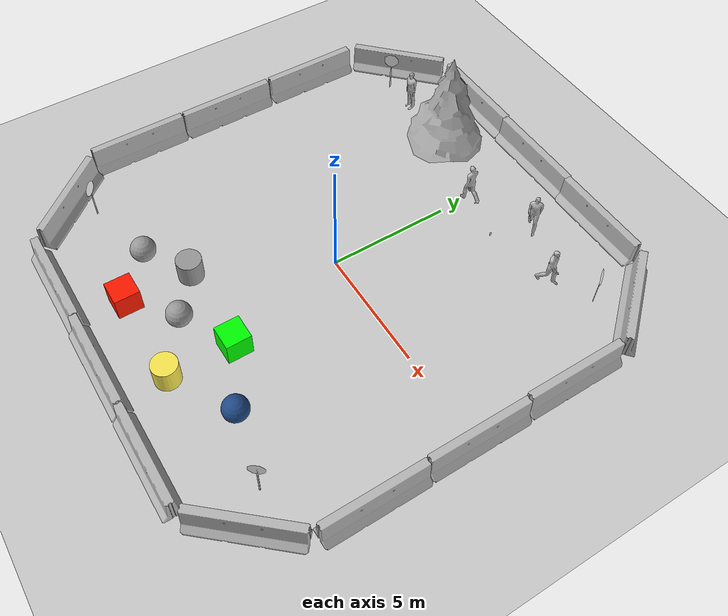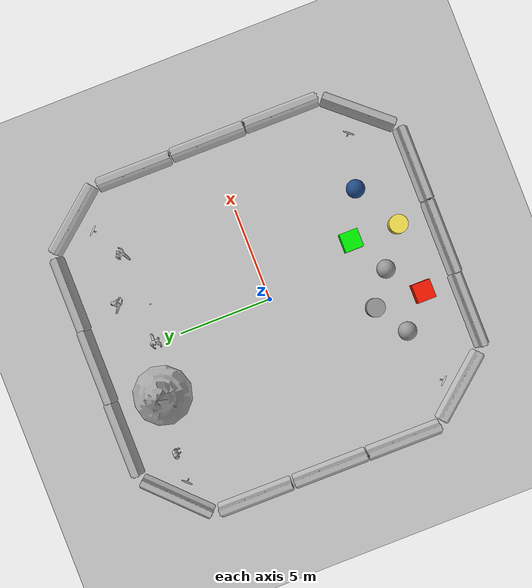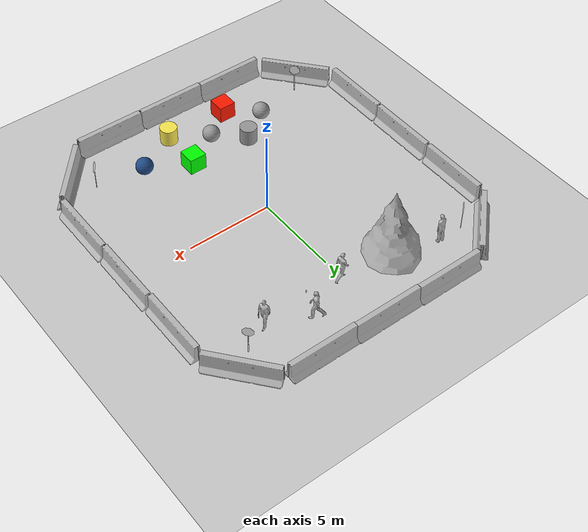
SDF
<sdf version='1.4'>
  <world name='default'>
    <!-- A global light source -->
    <include>
      <uri>model://sun</uri>
    </include>

    <!-- A ground plane -->
    <include>
      <uri>model://ground_plane</uri>
    </include>

    <physics type="ode">
      <real_time_update_rate>1000.0</real_time_update_rate>
      <max_step_size>0.001</max_step_size>
      <real_time_factor>1</real_time_factor>
      <ode>
        <solver>
          <type>quick</type>
          <iters>150</iters>
          <precon_iters>0</precon_iters>
          <sor>1.400000</sor>
          <use_dynamic_moi_rescaling>1</use_dynamic_moi_rescaling>
        </solver>
        <constraints>
          <cfm>0.00001</cfm>
          <erp>0.2</erp>
          <contact_max_correcting_vel>2000.000000</contact_max_correcting_vel>
          <contact_surface_layer>0.01000</contact_surface_layer>
        </constraints>
      </ode>
    </physics>

    <include>
       <uri>model://CloseArea2</uri>
    </include>

    <scene>
      <ambient>0.4 0.4 0.4 1</ambient>
      <background>0.7 0.7 0.7 1</background>
      <shadows>true</shadows>
    </scene>

    <gui fullscreen='0'>
      <camera name='user_camera'>
        <pose>0.8 0.0 12.0 0 1.5708 0</pose>
        <view_controller>orbit</view_controller>
      </camera>
    </gui>
  </world>
</sdf>

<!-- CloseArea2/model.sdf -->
<sdf version='1.7'>
  <model name='CloseArea2'>
    <link name='link_0'>
      <inertial>
        <mass>1</mass>
        <inertia>
          <ixx>0.1</ixx>
          <ixy>0</ixy>
          <ixz>0</ixz>
          <iyy>0.1</iyy>
          <iyz>0</iyz>
          <izz>0.1</izz>
        </inertia>
      </inertial>
      <pose>-4.13552 -6.09454 0.5 0 -0 0</pose>
      <visual name='visual'>
        <pose>0 0 0 0 -0 0</pose>
        <geometry>
          <sphere>
            <radius>0.5</radius>
          </sphere>
        </geometry>
        <material>
          <lighting>1</lighting>
          <script>
            <uri>file://media/materials/scripts/gazebo.material</uri>
            <name>Gazebo/Grey</name>
          </script>
          <shader type='pixel'/>
        </material>
        <transparency>0</transparency>
        <cast_shadows>1</cast_shadows>
      </visual>
      <collision name='collision'>
        <laser_retro>0</laser_retro>
        <max_contacts>10</max_contacts>
        <pose>0 0 0 0 -0 0</pose>
        <geometry>
          <sphere>
            <radius>0.5</radius>
          </sphere>
        </geometry>
        <surface>
          <friction>
            <ode>
              <mu>1</mu>
              <mu2>1</mu2>
              <fdir1>0 0 0</fdir1>
              <slip1>0</slip1>
              <slip2>0</slip2>
            </ode>
            <torsional>
              <coefficient>1</coefficient>
              <patch_radius>0</patch_radius>
              <surface_radius>0</surface_radius>
              <use_patch_radius>1</use_patch_radius>
              <ode>
                <slip>0</slip>
              </ode>
            </torsional>
          </friction>
          <bounce>
            <restitution_coefficient>0</restitution_coefficient>
            <threshold>1e+06</threshold>
          </bounce>
          <contact>
            <collide_without_contact>0</collide_without_contact>
            <collide_without_contact_bitmask>1</collide_without_contact_bitmask>
            <collide_bitmask>1</collide_bitmask>
            <ode>
              <soft_cfm>0</soft_cfm>
              <soft_erp>0.2</soft_erp>
              <kp>1e+13</kp>
              <kd>1</kd>
              <max_vel>0.01</max_vel>
              <min_depth>0</min_depth>
            </ode>
            <bullet>
              <split_impulse>1</split_impulse>
              <split_impulse_penetration_threshold>-0.01</split_impulse_penetration_threshold>
              <soft_cfm>0</soft_cfm>
              <soft_erp>0.2</soft_erp>
              <kp>1e+13</kp>
              <kd>1</kd>
            </bullet>
          </contact>
        </surface>
      </collision>
    </link>
    <link name='link_1'>
      <inertial>
        <mass>1</mass>
        <inertia>
          <ixx>0.166667</ixx>
          <ixy>0</ixy>
          <ixz>0</ixz>
          <iyy>0.166667</iyy>
          <iyz>0</iyz>
          <izz>0.166667</izz>
        </inertia>
        <pose>0 0 0 0 -0 0</pose>
      </inertial>
      <pose>-2.49394 -7.58408 0.5 0 -0 0</pose>
      <gravity>1</gravity>
      <self_collide>0</self_collide>
      <kinematic>0</kinematic>
      <enable_wind>0</enable_wind>
      <visual name='visual'>
        <pose>0 0 0 0 -0 0</pose>
        <geometry>
          <box>
            <size>1 1 1</size>
          </box>
        </geometry>
        <material>
          <lighting>1</lighting>
          <script>
            <uri>file://media/materials/scripts/gazebo.material</uri>
            <name>Gazebo/Grey</name>
          </script>
          <shader type='pixel'>
            <normal_map>__default__</normal_map>
          </shader>
          <ambient>1 0.098 0 1</ambient>
          <diffuse>0.7 0.7 0.7 1</diffuse>
          <specular>0.01 0.01 0.01 1</specular>
          <emissive>0 0 0 1</emissive>
        </material>
        <transparency>0</transparency>
        <cast_shadows>1</cast_shadows>
      </visual>
      <collision name='collision'>
        <laser_retro>0</laser_retro>
        <max_contacts>10</max_contacts>
        <pose>0 0 0 0 -0 0</pose>
        <geometry>
          <box>
            <size>1 1 1</size>
          </box>
        </geometry>
        <surface>
          <friction>
            <ode>
              <mu>1</mu>
              <mu2>1</mu2>
              <fdir1>0 0 0</fdir1>
              <slip1>0</slip1>
              <slip2>0</slip2>
            </ode>
            <torsional>
              <coefficient>1</coefficient>
              <patch_radius>0</patch_radius>
              <surface_radius>0</surface_radius>
              <use_patch_radius>1</use_patch_radius>
              <ode>
                <slip>0</slip>
              </ode>
            </torsional>
          </friction>
          <bounce>
            <restitution_coefficient>0</restitution_coefficient>
            <threshold>1e+06</threshold>
          </bounce>
          <contact>
            <collide_without_contact>0</collide_without_contact>
            <collide_without_contact_bitmask>1</collide_without_contact_bitmask>
            <collide_bitmask>1</collide_bitmask>
            <ode>
              <soft_cfm>0</soft_cfm>
              <soft_erp>0.2</soft_erp>
              <kp>1e+13</kp>
              <kd>1</kd>
              <max_vel>0.01</max_vel>
              <min_depth>0</min_depth>
            </ode>
            <bullet>
              <split_impulse>1</split_impulse>
              <split_impulse_penetration_threshold>-0.01</split_impulse_penetration_threshold>
              <soft_cfm>0</soft_cfm>
              <soft_erp>0.2</soft_erp>
              <kp>1e+13</kp>
              <kd>1</kd>
            </bullet>
          </contact>
        </surface>
      </collision>
    </link>
    <link name='link_2'>
      <inertial>
        <mass>1</mass>
        <inertia>
          <ixx>0.145833</ixx>
          <ixy>0</ixy>
          <ixz>0</ixz>
          <iyy>0.145833</iyy>
          <iyz>0</iyz>
          <izz>0.125</izz>
        </inertia>
      </inertial>
      <pose>-2.39473 -4.9579 0.5 0 -0 0</pose>
      <visual name='visual'>
        <pose>0 0 0 0 -0 0</pose>
        <geometry>
          <cylinder>
            <radius>0.5</radius>
            <length>1</length>
          </cylinder>
        </geometry>
        <material>
          <lighting>1</lighting>
          <script>
            <uri>file://media/materials/scripts/gazebo.material</uri>
            <name>Gazebo/Grey</name>
          </script>
          <shader type='pixel'/>
        </material>
        <transparency>0</transparency>
        <cast_shadows>1</cast_shadows>
      </visual>
      <collision name='collision'>
        <laser_retro>0</laser_retro>
        <max_contacts>10</max_contacts>
        <pose>0 0 0 0 -0 0</pose>
        <geometry>
          <cylinder>
            <radius>0.5</radius>
            <length>1</length>
          </cylinder>
        </geometry>
        <surface>
          <friction>
            <ode>
              <mu>1</mu>
              <mu2>1</mu2>
              <fdir1>0 0 0</fdir1>
              <slip1>0</slip1>
              <slip2>0</slip2>
            </ode>
            <torsional>
              <coefficient>1</coefficient>
              <patch_radius>0</patch_radius>
              <surface_radius>0</surface_radius>
              <use_patch_radius>1</use_patch_radius>
              <ode>
                <slip>0</slip>
              </ode>
            </torsional>
          </friction>
          <bounce>
            <restitution_coefficient>0</restitution_coefficient>
            <threshold>1e+06</threshold>
          </bounce>
          <contact>
            <collide_without_contact>0</collide_without_contact>
            <collide_without_contact_bitmask>1</collide_without_contact_bitmask>
            <collide_bitmask>1</collide_bitmask>
            <ode>
              <soft_cfm>0</soft_cfm>
              <soft_erp>0.2</soft_erp>
              <kp>1e+13</kp>
              <kd>1</kd>
              <max_vel>0.01</max_vel>
              <min_depth>0</min_depth>
            </ode>
            <bullet>
              <split_impulse>1</split_impulse>
              <split_impulse_penetration_threshold>-0.01</split_impulse_penetration_threshold>
              <soft_cfm>0</soft_cfm>
              <soft_erp>0.2</soft_erp>
              <kp>1e+13</kp>
              <kd>1</kd>
            </bullet>
          </contact>
        </surface>
      </collision>
    </link>
    <link name='link_3'>
      <inertial>
        <mass>1</mass>
        <inertia>
          <ixx>0.1</ixx>
          <ixy>0</ixy>
          <ixz>0</ixz>
          <iyy>0.1</iyy>
          <iyz>0</iyz>
          <izz>0.1</izz>
        </inertia>
        <pose>0 0 0 0 -0 0</pose>
      </inertial>
      <pose>-0.712996 -6.2141 0.5 0 -0 0</pose>
      <gravity>1</gravity>
      <self_collide>0</self_collide>
      <kinematic>0</kinematic>
      <enable_wind>0</enable_wind>
      <visual name='visual'>
        <pose>0 0 0 0 -0 0</pose>
        <geometry>
          <sphere>
            <radius>0.5</radius>
          </sphere>
        </geometry>
        <material>
          <lighting>1</lighting>
          <script>
            <uri>file://media/materials/scripts/gazebo.material</uri>
            <name>Gazebo/Grey</name>
          </script>
          <shader type='pixel'>
            <normal_map>__default__</normal_map>
          </shader>
          <ambient>0 0 0 1</ambient>
          <diffuse>0.7 0.7 0.7 1</diffuse>
          <specular>0.01 0.01 0.01 1</specular>
          <emissive>0 0 0 1</emissive>
        </material>
        <transparency>0</transparency>
        <cast_shadows>1</cast_shadows>
      </visual>
      <collision name='collision'>
        <laser_retro>0</laser_retro>
        <max_contacts>10</max_contacts>
        <pose>0 0 0 0 -0 0</pose>
        <geometry>
          <sphere>
            <radius>0.5</radius>
          </sphere>
        </geometry>
        <surface>
          <friction>
            <ode>
              <mu>1</mu>
              <mu2>1</mu2>
              <fdir1>0 0 0</fdir1>
              <slip1>0</slip1>
              <slip2>0</slip2>
            </ode>
            <torsional>
              <coefficient>1</coefficient>
              <patch_radius>0</patch_radius>
              <surface_radius>0</surface_radius>
              <use_patch_radius>1</use_patch_radius>
              <ode>
                <slip>0</slip>
              </ode>
            </torsional>
          </friction>
          <bounce>
            <restitution_coefficient>0</restitution_coefficient>
            <threshold>1e+06</threshold>
          </bounce>
          <contact>
            <collide_without_contact>0</collide_without_contact>
            <collide_without_contact_bitmask>1</collide_without_contact_bitmask>
            <collide_bitmask>1</collide_bitmask>
            <ode>
              <soft_cfm>0</soft_cfm>
              <soft_erp>0.2</soft_erp>
              <kp>1e+13</kp>
              <kd>1</kd>
              <max_vel>0.01</max_vel>
              <min_depth>0</min_depth>
            </ode>
            <bullet>
              <split_impulse>1</split_impulse>
              <split_impulse_penetration_threshold>-0.01</split_impulse_penetration_threshold>
              <soft_cfm>0</soft_cfm>
              <soft_erp>0.2</soft_erp>
              <kp>1e+13</kp>
              <kd>1</kd>
            </bullet>
          </contact>
        </surface>
      </collision>
    </link>
    <link name='link_4'>
      <inertial>
        <mass>1</mass>
        <inertia>
          <ixx>0.166667</ixx>
          <ixy>0</ixy>
          <ixz>0</ixz>
          <iyy>0.166667</iyy>
          <iyz>0</iyz>
          <izz>0.166667</izz>
        </inertia>
        <pose>0 0 0 0 -0 0</pose>
      </inertial>
      <pose>1.31431 -5.03886 0.5 0 -0 0</pose>
      <gravity>1</gravity>
      <self_collide>0</self_collide>
      <kinematic>0</kinematic>
      <enable_wind>0</enable_wind>
      <visual name='visual'>
        <pose>0 0 0 0 -0 0</pose>
        <geometry>
          <box>
            <size>1 1 1</size>
          </box>
        </geometry>
        <material>
          <lighting>1</lighting>
          <script>
            <uri>file://media/materials/scripts/gazebo.material</uri>
            <name>Gazebo/Grey</name>
          </script>
          <shader type='pixel'>
            <normal_map>__default__</normal_map>
          </shader>
          <ambient>0 1 0 1</ambient>
          <diffuse>0.7 0.7 0.7 1</diffuse>
          <specular>0.01 0.01 0.01 1</specular>
          <emissive>0 0 0 1</emissive>
        </material>
        <transparency>0</transparency>
        <cast_shadows>1</cast_shadows>
      </visual>
      <collision name='collision'>
        <laser_retro>0</laser_retro>
        <max_contacts>10</max_contacts>
        <pose>0 0 0 0 -0 0</pose>
        <geometry>
          <box>
            <size>1 1 1</size>
          </box>
        </geometry>
        <surface>
          <friction>
            <ode>
              <mu>1</mu>
              <mu2>1</mu2>
              <fdir1>0 0 0</fdir1>
              <slip1>0</slip1>
              <slip2>0</slip2>
            </ode>
            <torsional>
              <coefficient>1</coefficient>
              <patch_radius>0</patch_radius>
              <surface_radius>0</surface_radius>
              <use_patch_radius>1</use_patch_radius>
              <ode>
                <slip>0</slip>
              </ode>
            </torsional>
          </friction>
          <bounce>
            <restitution_coefficient>0</restitution_coefficient>
            <threshold>1e+06</threshold>
          </bounce>
          <contact>
            <collide_without_contact>0</collide_without_contact>
            <collide_without_contact_bitmask>1</collide_without_contact_bitmask>
            <collide_bitmask>1</collide_bitmask>
            <ode>
              <soft_cfm>0</soft_cfm>
              <soft_erp>0.2</soft_erp>
              <kp>1e+13</kp>
              <kd>1</kd>
              <max_vel>0.01</max_vel>
              <min_depth>0</min_depth>
            </ode>
            <bullet>
              <split_impulse>1</split_impulse>
              <split_impulse_penetration_threshold>-0.01</split_impulse_penetration_threshold>
              <soft_cfm>0</soft_cfm>
              <soft_erp>0.2</soft_erp>
              <kp>1e+13</kp>
              <kd>1</kd>
            </bullet>
          </contact>
        </surface>
      </collision>
    </link>
    <link name='link_5'>
      <inertial>
        <mass>1</mass>
        <inertia>
          <ixx>0.1</ixx>
          <ixy>0</ixy>
          <ixz>0</ixz>
          <iyy>0.1</iyy>
          <iyz>0</iyz>
          <izz>0.1</izz>
        </inertia>
        <pose>0 0 0 0 -0 0</pose>
      </inertial>
      <pose>3.75251 -6.24602 0.5 0 -0 0</pose>
      <gravity>1</gravity>
      <self_collide>0</self_collide>
      <kinematic>0</kinematic>
      <enable_wind>0</enable_wind>
      <visual name='visual'>
        <pose>0 0 0 0 -0 0</pose>
        <geometry>
          <sphere>
            <radius>0.5</radius>
          </sphere>
        </geometry>
        <material>
          <lighting>1</lighting>
          <script>
            <uri>file://media/materials/scripts/gazebo.material</uri>
            <name>Gazebo/Grey</name>
          </script>
          <shader type='pixel'>
            <normal_map>__default__</normal_map>
          </shader>
          <ambient>0.125 0.29 0.529 1</ambient>
          <diffuse>0.7 0.7 0.7 1</diffuse>
          <specular>0.01 0.01 0.01 1</specular>
          <emissive>0 0 0 1</emissive>
        </material>
        <transparency>0</transparency>
        <cast_shadows>1</cast_shadows>
      </visual>
      <collision name='collision'>
        <laser_retro>0</laser_retro>
        <max_contacts>10</max_contacts>
        <pose>0 0 0 0 -0 0</pose>
        <geometry>
          <sphere>
            <radius>0.5</radius>
          </sphere>
        </geometry>
        <surface>
          <friction>
            <ode>
              <mu>1</mu>
              <mu2>1</mu2>
              <fdir1>0 0 0</fdir1>
              <slip1>0</slip1>
              <slip2>0</slip2>
            </ode>
            <torsional>
              <coefficient>1</coefficient>
              <patch_radius>0</patch_radius>
              <surface_radius>0</surface_radius>
              <use_patch_radius>1</use_patch_radius>
              <ode>
                <slip>0</slip>
              </ode>
            </torsional>
          </friction>
          <bounce>
            <restitution_coefficient>0</restitution_coefficient>
            <threshold>1e+06</threshold>
          </bounce>
          <contact>
            <collide_without_contact>0</collide_without_contact>
            <collide_without_contact_bitmask>1</collide_without_contact_bitmask>
            <collide_bitmask>1</collide_bitmask>
            <ode>
              <soft_cfm>0</soft_cfm>
              <soft_erp>0.2</soft_erp>
              <kp>1e+13</kp>
              <kd>1</kd>
              <max_vel>0.01</max_vel>
              <min_depth>0</min_depth>
            </ode>
            <bullet>
              <split_impulse>1</split_impulse>
              <split_impulse_penetration_threshold>-0.01</split_impulse_penetration_threshold>
              <soft_cfm>0</soft_cfm>
              <soft_erp>0.2</soft_erp>
              <kp>1e+13</kp>
              <kd>1</kd>
            </bullet>
          </contact>
        </surface>
      </collision>
    </link>
    <link name='link_6'>
      <inertial>
        <mass>1</mass>
        <inertia>
          <ixx>0.145833</ixx>
          <ixy>0</ixy>
          <ixz>0</ixz>
          <iyy>0.145833</iyy>
          <iyz>0</iyz>
          <izz>0.125</izz>
        </inertia>
        <pose>0 0 0 0 -0 0</pose>
      </inertial>
      <pose>1.22866 -7.62915 0.5 0 -0 0</pose>
      <gravity>1</gravity>
      <self_collide>0</self_collide>
      <kinematic>0</kinematic>
      <enable_wind>0</enable_wind>
      <visual name='visual'>
        <pose>0 0 0 0 -0 0</pose>
        <geometry>
          <cylinder>
            <radius>0.5</radius>
            <length>1</length>
          </cylinder>
        </geometry>
        <material>
          <lighting>1</lighting>
          <script>
            <uri>file://media/materials/scripts/gazebo.material</uri>
            <name>Gazebo/Grey</name>
          </script>
          <shader type='pixel'>
            <normal_map>__default__</normal_map>
          </shader>
          <ambient>0.988 0.914 0.31 1</ambient>
          <diffuse>0.7 0.7 0.7 1</diffuse>
          <specular>0.01 0.01 0.01 1</specular>
          <emissive>0 0 0 1</emissive>
        </material>
        <transparency>0</transparency>
        <cast_shadows>1</cast_shadows>
      </visual>
      <collision name='collision'>
        <laser_retro>0</laser_retro>
        <max_contacts>10</max_contacts>
        <pose>0 0 0 0 -0 0</pose>
        <geometry>
          <cylinder>
            <radius>0.5</radius>
            <length>1</length>
          </cylinder>
        </geometry>
        <surface>
          <friction>
            <ode>
              <mu>1</mu>
              <mu2>1</mu2>
              <fdir1>0 0 0</fdir1>
              <slip1>0</slip1>
              <slip2>0</slip2>
            </ode>
            <torsional>
              <coefficient>1</coefficient>
              <patch_radius>0</patch_radius>
              <surface_radius>0</surface_radius>
              <use_patch_radius>1</use_patch_radius>
              <ode>
                <slip>0</slip>
              </ode>
            </torsional>
          </friction>
          <bounce>
            <restitution_coefficient>0</restitution_coefficient>
            <threshold>1e+06</threshold>
          </bounce>
          <contact>
            <collide_without_contact>0</collide_without_contact>
            <collide_without_contact_bitmask>1</collide_without_contact_bitmask>
            <collide_bitmask>1</collide_bitmask>
            <ode>
              <soft_cfm>0</soft_cfm>
              <soft_erp>0.2</soft_erp>
              <kp>1e+13</kp>
              <kd>1</kd>
              <max_vel>0.01</max_vel>
              <min_depth>0</min_depth>
            </ode>
            <bullet>
              <split_impulse>1</split_impulse>
              <split_impulse_penetration_threshold>-0.01</split_impulse_penetration_threshold>
              <soft_cfm>0</soft_cfm>
              <soft_erp>0.2</soft_erp>
              <kp>1e+13</kp>
              <kd>1</kd>
            </bullet>
          </contact>
        </surface>
      </collision>
    </link>
    <model name='Stop Sign'>
      <static>1</static>
      <link name='link'>
        <collision name='collision'>
          <geometry>
            <mesh>
              <uri>model://stop_sign/meshes/stop_sign.dae</uri>
            </mesh>
          </geometry>
          <max_contacts>10</max_contacts>
          <surface>
            <contact>
              <ode/>
            </contact>
            <bounce/>
            <friction>
              <torsional>
                <ode/>
              </torsional>
              <ode/>
            </friction>
          </surface>
        </collision>
        <visual name='visual'>
          <geometry>
            <mesh>
              <uri>model://stop_sign/meshes/stop_sign.dae</uri>
            </mesh>
          </geometry>
          <material>
            <script>
              <uri>model://stop_sign/materials/scripts</uri>
              <uri>model://stop_sign/materials/textures</uri>
              <name>StopSign/Diffuse</name>
            </script>
          </material>
        </visual>
        <self_collide>0</self_collide>
        <enable_wind>0</enable_wind>
        <kinematic>0</kinematic>
      </link>
      <pose>-7.22822 7.37397 0.007017 0 -0 0.817531</pose>
    </model>
    <model name='Stop Sign_clone'>
      <static>1</static>
      <link name='link'>
        <collision name='collision'>
          <geometry>
            <mesh>
              <uri>model://stop_sign/meshes/stop_sign.dae</uri>
            </mesh>
          </geometry>
          <max_contacts>10</max_contacts>
          <surface>
            <contact>
              <ode/>
            </contact>
            <bounce/>
            <friction>
              <torsional>
                <ode/>
              </torsional>
              <ode/>
            </friction>
          </surface>
        </collision>
        <visual name='visual'>
          <geometry>
            <mesh>
              <uri>model://stop_sign/meshes/stop_sign.dae</uri>
            </mesh>
          </geometry>
          <material>
            <script>
              <uri>model://stop_sign/materials/scripts</uri>
              <uri>model://stop_sign/materials/textures</uri>
              <name>StopSign/Diffuse</name>
            </script>
          </material>
        </visual>
        <self_collide>0</self_collide>
        <enable_wind>0</enable_wind>
        <kinematic>0</kinematic>
      </link>
      <pose>-7.13821 -6.82157 0.007016 0 -0 2.33967</pose>
    </model>
    <model name='Stop Sign_clone_0'>
      <static>1</static>
      <link name='link'>
        <collision name='collision'>
          <geometry>
            <mesh>
              <uri>model://stop_sign/meshes/stop_sign.dae</uri>
            </mesh>
          </geometry>
          <max_contacts>10</max_contacts>
          <surface>
            <contact>
              <ode/>
            </contact>
            <bounce/>
            <friction>
              <torsional>
                <ode/>
              </torsional>
              <ode/>
            </friction>
          </surface>
        </collision>
        <visual name='visual'>
          <geometry>
            <mesh>
              <uri>model://stop_sign/meshes/stop_sign.dae</uri>
            </mesh>
          </geometry>
          <material>
            <script>
              <uri>model://stop_sign/materials/scripts</uri>
              <uri>model://stop_sign/materials/textures</uri>
              <name>StopSign/Diffuse</name>
            </script>
          </material>
        </visual>
        <self_collide>0</self_collide>
        <enable_wind>0</enable_wind>
        <kinematic>0</kinematic>
      </link>
      <pose>6.50021 -6.86088 0.007016 0 0 -2.26485</pose>
    </model>
    <model name='Stop Sign_clone_1'>
      <static>1</static>
      <link name='link'>
        <collision name='collision'>
          <geometry>
            <mesh>
              <uri>model://stop_sign/meshes/stop_sign.dae</uri>
            </mesh>
          </geometry>
          <max_contacts>10</max_contacts>
          <surface>
            <contact>
              <ode/>
            </contact>
            <bounce/>
            <friction>
              <torsional>
                <ode/>
              </torsional>
              <ode/>
            </friction>
          </surface>
        </collision>
        <visual name='visual'>
          <geometry>
            <mesh>
              <uri>model://stop_sign/meshes/stop_sign.dae</uri>
            </mesh>
          </geometry>
          <material>
            <script>
              <uri>model://stop_sign/materials/scripts</uri>
              <uri>model://stop_sign/materials/textures</uri>
              <name>StopSign/Diffuse</name>
            </script>
          </material>
        </visual>
        <self_collide>0</self_collide>
        <enable_wind>0</enable_wind>
        <kinematic>0</kinematic>
      </link>
      <pose>6.57883 7.20988 0.007016 0 0 -0.824905</pose>
    </model>
    <model name='jersey_barrier'>
      <static>1</static>
      <link name='link'>
        <visual name='visual'>
          <geometry>
            <mesh>
              <uri>model://jersey_barrier/meshes/jersey_barrier.dae</uri>
            </mesh>
          </geometry>
        </visual>
        <collision name='upright'>
          <pose>0 0 0.5715 0 -0 0</pose>
          <geometry>
            <box>
              <size>4.06542 0.3063 1.143</size>
            </box>
          </geometry>
          <max_contacts>10</max_contacts>
          <surface>
            <contact>
              <ode/>
            </contact>
            <bounce/>
            <friction>
              <torsional>
                <ode/>
              </torsional>
              <ode/>
            </friction>
          </surface>
        </collision>
        <collision name='base'>
          <pose>0 0 0.032258 0 -0 0</pose>
          <geometry>
            <box>
              <size>4.06542 0.8107 0.064516</size>
            </box>
          </geometry>
          <max_contacts>10</max_contacts>
          <surface>
            <contact>
              <ode/>
            </contact>
            <bounce/>
            <friction>
              <torsional>
                <ode/>
              </torsional>
              <ode/>
            </friction>
          </surface>
        </collision>
        <collision name='base2'>
          <pose>0 0 0.1 0 -0 0</pose>
          <geometry>
            <box>
              <size>4.06542 0.65 0.1</size>
            </box>
          </geometry>
          <max_contacts>10</max_contacts>
          <surface>
            <contact>
              <ode/>
            </contact>
            <bounce/>
            <friction>
              <torsional>
                <ode/>
              </torsional>
              <ode/>
            </friction>
          </surface>
        </collision>
        <collision name='base3'>
          <pose>0 0 0.2 0 -0 0</pose>
          <geometry>
            <box>
              <size>4.06542 0.5 0.1</size>
            </box>
          </geometry>
          <max_contacts>10</max_contacts>
          <surface>
            <contact>
              <ode/>
            </contact>
            <bounce/>
            <friction>
              <torsional>
                <ode/>
              </torsional>
              <ode/>
            </friction>
          </surface>
        </collision>
        <collision name='left-angle'>
          <pose>0 -0.224 0.2401 0.9 -0 0</pose>
          <geometry>
            <box>
              <size>4.06542 0.5 0.064516</size>
            </box>
          </geometry>
          <max_contacts>10</max_contacts>
          <surface>
            <contact>
              <ode/>
            </contact>
            <bounce/>
            <friction>
              <torsional>
                <ode/>
              </torsional>
              <ode/>
            </friction>
          </surface>
        </collision>
        <collision name='right-angle'>
          <pose>0 0.224 0.2401 -0.9 0 0</pose>
          <geometry>
            <box>
              <size>4.06542 0.5 0.064516</size>
            </box>
          </geometry>
          <max_contacts>10</max_contacts>
          <surface>
            <contact>
              <ode/>
            </contact>
            <bounce/>
            <friction>
              <torsional>
                <ode/>
              </torsional>
              <ode/>
            </friction>
          </surface>
        </collision>
        <self_collide>0</self_collide>
        <enable_wind>0</enable_wind>
        <kinematic>0</kinematic>
      </link>
      <pose>7.49146 -7.87127 0.005921 0 -0 0.854903</pose>
    </model>
    <model name='jersey_barrier_clone'>
      <static>1</static>
      <link name='link'>
        <visual name='visual'>
          <geometry>
            <mesh>
              <uri>model://jersey_barrier/meshes/jersey_barrier.dae</uri>
            </mesh>
          </geometry>
        </visual>
        <collision name='upright'>
          <pose>0 0 0.5715 0 -0 0</pose>
          <geometry>
            <box>
              <size>4.06542 0.3063 1.143</size>
            </box>
          </geometry>
          <max_contacts>10</max_contacts>
          <surface>
            <contact>
              <ode/>
            </contact>
            <bounce/>
            <friction>
              <torsional>
                <ode/>
              </torsional>
              <ode/>
            </friction>
          </surface>
        </collision>
        <collision name='base'>
          <pose>0 0 0.032258 0 -0 0</pose>
          <geometry>
            <box>
              <size>4.06542 0.8107 0.064516</size>
            </box>
          </geometry>
          <max_contacts>10</max_contacts>
          <surface>
            <contact>
              <ode/>
            </contact>
            <bounce/>
            <friction>
              <torsional>
                <ode/>
              </torsional>
              <ode/>
            </friction>
          </surface>
        </collision>
        <collision name='base2'>
          <pose>0 0 0.1 0 -0 0</pose>
          <geometry>
            <box>
              <size>4.06542 0.65 0.1</size>
            </box>
          </geometry>
          <max_contacts>10</max_contacts>
          <surface>
            <contact>
              <ode/>
            </contact>
            <bounce/>
            <friction>
              <torsional>
                <ode/>
              </torsional>
              <ode/>
            </friction>
          </surface>
        </collision>
        <collision name='base3'>
          <pose>0 0 0.2 0 -0 0</pose>
          <geometry>
            <box>
              <size>4.06542 0.5 0.1</size>
            </box>
          </geometry>
          <max_contacts>10</max_contacts>
          <surface>
            <contact>
              <ode/>
            </contact>
            <bounce/>
            <friction>
              <torsional>
                <ode/>
              </torsional>
              <ode/>
            </friction>
          </surface>
        </collision>
        <collision name='left-angle'>
          <pose>0 -0.224 0.2401 0.9 -0 0</pose>
          <geometry>
            <box>
              <size>4.06542 0.5 0.064516</size>
            </box>
          </geometry>
          <max_contacts>10</max_contacts>
          <surface>
            <contact>
              <ode/>
            </contact>
            <bounce/>
            <friction>
              <torsional>
                <ode/>
              </torsional>
              <ode/>
            </friction>
          </surface>
        </collision>
        <collision name='right-angle'>
          <pose>0 0.224 0.2401 -0.9 0 0</pose>
          <geometry>
            <box>
              <size>4.06542 0.5 0.064516</size>
            </box>
          </geometry>
          <max_contacts>10</max_contacts>
          <surface>
            <contact>
              <ode/>
            </contact>
            <bounce/>
            <friction>
              <torsional>
                <ode/>
              </torsional>
              <ode/>
            </friction>
          </surface>
        </collision>
        <self_collide>0</self_collide>
        <enable_wind>0</enable_wind>
        <kinematic>0</kinematic>
      </link>
      <pose>7.60825 8.09586 0.003838 0 0 -0.877727</pose>
    </model>
    <model name='jersey_barrier_clone_0'>
      <static>1</static>
      <link name='link'>
        <visual name='visual'>
          <geometry>
            <mesh>
              <uri>model://jersey_barrier/meshes/jersey_barrier.dae</uri>
            </mesh>
          </geometry>
        </visual>
        <collision name='upright'>
          <pose>0 0 0.5715 0 -0 0</pose>
          <geometry>
            <box>
              <size>4.06542 0.3063 1.143</size>
            </box>
          </geometry>
          <max_contacts>10</max_contacts>
          <surface>
            <contact>
              <ode/>
            </contact>
            <bounce/>
            <friction>
              <torsional>
                <ode/>
              </torsional>
              <ode/>
            </friction>
          </surface>
        </collision>
        <collision name='base'>
          <pose>0 0 0.032258 0 -0 0</pose>
          <geometry>
            <box>
              <size>4.06542 0.8107 0.064516</size>
            </box>
          </geometry>
          <max_contacts>10</max_contacts>
          <surface>
            <contact>
              <ode/>
            </contact>
            <bounce/>
            <friction>
              <torsional>
                <ode/>
              </torsional>
              <ode/>
            </friction>
          </surface>
        </collision>
        <collision name='base2'>
          <pose>0 0 0.1 0 -0 0</pose>
          <geometry>
            <box>
              <size>4.06542 0.65 0.1</size>
            </box>
          </geometry>
          <max_contacts>10</max_contacts>
          <surface>
            <contact>
              <ode/>
            </contact>
            <bounce/>
            <friction>
              <torsional>
                <ode/>
              </torsional>
              <ode/>
            </friction>
          </surface>
        </collision>
        <collision name='base3'>
          <pose>0 0 0.2 0 -0 0</pose>
          <geometry>
            <box>
              <size>4.06542 0.5 0.1</size>
            </box>
          </geometry>
          <max_contacts>10</max_contacts>
          <surface>
            <contact>
              <ode/>
            </contact>
            <bounce/>
            <friction>
              <torsional>
                <ode/>
              </torsional>
              <ode/>
            </friction>
          </surface>
        </collision>
        <collision name='left-angle'>
          <pose>0 -0.224 0.2401 0.9 -0 0</pose>
          <geometry>
            <box>
              <size>4.06542 0.5 0.064516</size>
            </box>
          </geometry>
          <max_contacts>10</max_contacts>
          <surface>
            <contact>
              <ode/>
            </contact>
            <bounce/>
            <friction>
              <torsional>
                <ode/>
              </torsional>
              <ode/>
            </friction>
          </surface>
        </collision>
        <collision name='right-angle'>
          <pose>0 0.224 0.2401 -0.9 0 0</pose>
          <geometry>
            <box>
              <size>4.06542 0.5 0.064516</size>
            </box>
          </geometry>
          <max_contacts>10</max_contacts>
          <surface>
            <contact>
              <ode/>
            </contact>
            <bounce/>
            <friction>
              <torsional>
                <ode/>
              </torsional>
              <ode/>
            </friction>
          </surface>
        </collision>
        <self_collide>0</self_collide>
        <enable_wind>0</enable_wind>
        <kinematic>0</kinematic>
      </link>
      <pose>3.88632 -9.57923 0.003838 0 -0 0</pose>
    </model>
    <model name='jersey_barrier_clone_1'>
      <static>1</static>
      <link name='link'>
        <visual name='visual'>
          <geometry>
            <mesh>
              <uri>model://jersey_barrier/meshes/jersey_barrier.dae</uri>
            </mesh>
          </geometry>
        </visual>
        <collision name='upright'>
          <pose>0 0 0.5715 0 -0 0</pose>
          <geometry>
            <box>
              <size>4.06542 0.3063 1.143</size>
            </box>
          </geometry>
          <max_contacts>10</max_contacts>
          <surface>
            <contact>
              <ode/>
            </contact>
            <bounce/>
            <friction>
              <torsional>
                <ode/>
              </torsional>
              <ode/>
            </friction>
          </surface>
        </collision>
        <collision name='base'>
          <pose>0 0 0.032258 0 -0 0</pose>
          <geometry>
            <box>
              <size>4.06542 0.8107 0.064516</size>
            </box>
          </geometry>
          <max_contacts>10</max_contacts>
          <surface>
            <contact>
              <ode/>
            </contact>
            <bounce/>
            <friction>
              <torsional>
                <ode/>
              </torsional>
              <ode/>
            </friction>
          </surface>
        </collision>
        <collision name='base2'>
          <pose>0 0 0.1 0 -0 0</pose>
          <geometry>
            <box>
              <size>4.06542 0.65 0.1</size>
            </box>
          </geometry>
          <max_contacts>10</max_contacts>
          <surface>
            <contact>
              <ode/>
            </contact>
            <bounce/>
            <friction>
              <torsional>
                <ode/>
              </torsional>
              <ode/>
            </friction>
          </surface>
        </collision>
        <collision name='base3'>
          <pose>0 0 0.2 0 -0 0</pose>
          <geometry>
            <box>
              <size>4.06542 0.5 0.1</size>
            </box>
          </geometry>
          <max_contacts>10</max_contacts>
          <surface>
            <contact>
              <ode/>
            </contact>
            <bounce/>
            <friction>
              <torsional>
                <ode/>
              </torsional>
              <ode/>
            </friction>
          </surface>
        </collision>
        <collision name='left-angle'>
          <pose>0 -0.224 0.2401 0.9 -0 0</pose>
          <geometry>
            <box>
              <size>4.06542 0.5 0.064516</size>
            </box>
          </geometry>
          <max_contacts>10</max_contacts>
          <surface>
            <contact>
              <ode/>
            </contact>
            <bounce/>
            <friction>
              <torsional>
                <ode/>
              </torsional>
              <ode/>
            </friction>
          </surface>
        </collision>
        <collision name='right-angle'>
          <pose>0 0.224 0.2401 -0.9 0 0</pose>
          <geometry>
            <box>
              <size>4.06542 0.5 0.064516</size>
            </box>
          </geometry>
          <max_contacts>10</max_contacts>
          <surface>
            <contact>
              <ode/>
            </contact>
            <bounce/>
            <friction>
              <torsional>
                <ode/>
              </torsional>
              <ode/>
            </friction>
          </surface>
        </collision>
        <self_collide>0</self_collide>
        <enable_wind>0</enable_wind>
        <kinematic>0</kinematic>
      </link>
      <pose>-0.211579 -9.56071 0.003838 0 -0 0</pose>
    </model>
    <model name='jersey_barrier_clone_2'>
      <static>1</static>
      <link name='link'>
        <visual name='visual'>
          <geometry>
            <mesh>
              <uri>model://jersey_barrier/meshes/jersey_barrier.dae</uri>
            </mesh>
          </geometry>
        </visual>
        <collision name='upright'>
          <pose>0 0 0.5715 0 -0 0</pose>
          <geometry>
            <box>
              <size>4.06542 0.3063 1.143</size>
            </box>
          </geometry>
          <max_contacts>10</max_contacts>
          <surface>
            <contact>
              <ode/>
            </contact>
            <bounce/>
            <friction>
              <torsional>
                <ode/>
              </torsional>
              <ode/>
            </friction>
          </surface>
        </collision>
        <collision name='base'>
          <pose>0 0 0.032258 0 -0 0</pose>
          <geometry>
            <box>
              <size>4.06542 0.8107 0.064516</size>
            </box>
          </geometry>
          <max_contacts>10</max_contacts>
          <surface>
            <contact>
              <ode/>
            </contact>
            <bounce/>
            <friction>
              <torsional>
                <ode/>
              </torsional>
              <ode/>
            </friction>
          </surface>
        </collision>
        <collision name='base2'>
          <pose>0 0 0.1 0 -0 0</pose>
          <geometry>
            <box>
              <size>4.06542 0.65 0.1</size>
            </box>
          </geometry>
          <max_contacts>10</max_contacts>
          <surface>
            <contact>
              <ode/>
            </contact>
            <bounce/>
            <friction>
              <torsional>
                <ode/>
              </torsional>
              <ode/>
            </friction>
          </surface>
        </collision>
        <collision name='base3'>
          <pose>0 0 0.2 0 -0 0</pose>
          <geometry>
            <box>
              <size>4.06542 0.5 0.1</size>
            </box>
          </geometry>
          <max_contacts>10</max_contacts>
          <surface>
            <contact>
              <ode/>
            </contact>
            <bounce/>
            <friction>
              <torsional>
                <ode/>
              </torsional>
              <ode/>
            </friction>
          </surface>
        </collision>
        <collision name='left-angle'>
          <pose>0 -0.224 0.2401 0.9 -0 0</pose>
          <geometry>
            <box>
              <size>4.06542 0.5 0.064516</size>
            </box>
          </geometry>
          <max_contacts>10</max_contacts>
          <surface>
            <contact>
              <ode/>
            </contact>
            <bounce/>
            <friction>
              <torsional>
                <ode/>
              </torsional>
              <ode/>
            </friction>
          </surface>
        </collision>
        <collision name='right-angle'>
          <pose>0 0.224 0.2401 -0.9 0 0</pose>
          <geometry>
            <box>
              <size>4.06542 0.5 0.064516</size>
            </box>
          </geometry>
          <max_contacts>10</max_contacts>
          <surface>
            <contact>
              <ode/>
            </contact>
            <bounce/>
            <friction>
              <torsional>
                <ode/>
              </torsional>
              <ode/>
            </friction>
          </surface>
        </collision>
        <self_collide>0</self_collide>
        <enable_wind>0</enable_wind>
        <kinematic>0</kinematic>
      </link>
      <pose>-4.26169 -9.50069 0.003838 0 -0 0</pose>
    </model>
    <model name='jersey_barrier_clone_3'>
      <static>1</static>
      <link name='link'>
        <visual name='visual'>
          <geometry>
            <mesh>
              <uri>model://jersey_barrier/meshes/jersey_barrier.dae</uri>
            </mesh>
          </geometry>
        </visual>
        <collision name='upright'>
          <pose>0 0 0.5715 0 -0 0</pose>
          <geometry>
            <box>
              <size>4.06542 0.3063 1.143</size>
            </box>
          </geometry>
          <max_contacts>10</max_contacts>
          <surface>
            <contact>
              <ode/>
            </contact>
            <bounce/>
            <friction>
              <torsional>
                <ode/>
              </torsional>
              <ode/>
            </friction>
          </surface>
        </collision>
        <collision name='base'>
          <pose>0 0 0.032258 0 -0 0</pose>
          <geometry>
            <box>
              <size>4.06542 0.8107 0.064516</size>
            </box>
          </geometry>
          <max_contacts>10</max_contacts>
          <surface>
            <contact>
              <ode/>
            </contact>
            <bounce/>
            <friction>
              <torsional>
                <ode/>
              </torsional>
              <ode/>
            </friction>
          </surface>
        </collision>
        <collision name='base2'>
          <pose>0 0 0.1 0 -0 0</pose>
          <geometry>
            <box>
              <size>4.06542 0.65 0.1</size>
            </box>
          </geometry>
          <max_contacts>10</max_contacts>
          <surface>
            <contact>
              <ode/>
            </contact>
            <bounce/>
            <friction>
              <torsional>
                <ode/>
              </torsional>
              <ode/>
            </friction>
          </surface>
        </collision>
        <collision name='base3'>
          <pose>0 0 0.2 0 -0 0</pose>
          <geometry>
            <box>
              <size>4.06542 0.5 0.1</size>
            </box>
          </geometry>
          <max_contacts>10</max_contacts>
          <surface>
            <contact>
              <ode/>
            </contact>
            <bounce/>
            <friction>
              <torsional>
                <ode/>
              </torsional>
              <ode/>
            </friction>
          </surface>
        </collision>
        <collision name='left-angle'>
          <pose>0 -0.224 0.2401 0.9 -0 0</pose>
          <geometry>
            <box>
              <size>4.06542 0.5 0.064516</size>
            </box>
          </geometry>
          <max_contacts>10</max_contacts>
          <surface>
            <contact>
              <ode/>
            </contact>
            <bounce/>
            <friction>
              <torsional>
                <ode/>
              </torsional>
              <ode/>
            </friction>
          </surface>
        </collision>
        <collision name='right-angle'>
          <pose>0 0.224 0.2401 -0.9 0 0</pose>
          <geometry>
            <box>
              <size>4.06542 0.5 0.064516</size>
            </box>
          </geometry>
          <max_contacts>10</max_contacts>
          <surface>
            <contact>
              <ode/>
            </contact>
            <bounce/>
            <friction>
              <torsional>
                <ode/>
              </torsional>
              <ode/>
            </friction>
          </surface>
        </collision>
        <self_collide>0</self_collide>
        <enable_wind>0</enable_wind>
        <kinematic>0</kinematic>
      </link>
      <pose>-7.84176 -7.62913 0.003838 0 0 -0.867873</pose>
    </model>
    <model name='jersey_barrier_clone_4'>
      <static>1</static>
      <link name='link'>
        <visual name='visual'>
          <geometry>
            <mesh>
              <uri>model://jersey_barrier/meshes/jersey_barrier.dae</uri>
            </mesh>
          </geometry>
        </visual>
        <collision name='upright'>
          <pose>0 0 0.5715 0 -0 0</pose>
          <geometry>
            <box>
              <size>4.06542 0.3063 1.143</size>
            </box>
          </geometry>
          <max_contacts>10</max_contacts>
          <surface>
            <contact>
              <ode/>
            </contact>
            <bounce/>
            <friction>
              <torsional>
                <ode/>
              </torsional>
              <ode/>
            </friction>
          </surface>
        </collision>
        <collision name='base'>
          <pose>0 0 0.032258 0 -0 0</pose>
          <geometry>
            <box>
              <size>4.06542 0.8107 0.064516</size>
            </box>
          </geometry>
          <max_contacts>10</max_contacts>
          <surface>
            <contact>
              <ode/>
            </contact>
            <bounce/>
            <friction>
              <torsional>
                <ode/>
              </torsional>
              <ode/>
            </friction>
          </surface>
        </collision>
        <collision name='base2'>
          <pose>0 0 0.1 0 -0 0</pose>
          <geometry>
            <box>
              <size>4.06542 0.65 0.1</size>
            </box>
          </geometry>
          <max_contacts>10</max_contacts>
          <surface>
            <contact>
              <ode/>
            </contact>
            <bounce/>
            <friction>
              <torsional>
                <ode/>
              </torsional>
              <ode/>
            </friction>
          </surface>
        </collision>
        <collision name='base3'>
          <pose>0 0 0.2 0 -0 0</pose>
          <geometry>
            <box>
              <size>4.06542 0.5 0.1</size>
            </box>
          </geometry>
          <max_contacts>10</max_contacts>
          <surface>
            <contact>
              <ode/>
            </contact>
            <bounce/>
            <friction>
              <torsional>
                <ode/>
              </torsional>
              <ode/>
            </friction>
          </surface>
        </collision>
        <collision name='left-angle'>
          <pose>0 -0.224 0.2401 0.9 -0 0</pose>
          <geometry>
            <box>
              <size>4.06542 0.5 0.064516</size>
            </box>
          </geometry>
          <max_contacts>10</max_contacts>
          <surface>
            <contact>
              <ode/>
            </contact>
            <bounce/>
            <friction>
              <torsional>
                <ode/>
              </torsional>
              <ode/>
            </friction>
          </surface>
        </collision>
        <collision name='right-angle'>
          <pose>0 0.224 0.2401 -0.9 0 0</pose>
          <geometry>
            <box>
              <size>4.06542 0.5 0.064516</size>
            </box>
          </geometry>
          <max_contacts>10</max_contacts>
          <surface>
            <contact>
              <ode/>
            </contact>
            <bounce/>
            <friction>
              <torsional>
                <ode/>
              </torsional>
              <ode/>
            </friction>
          </surface>
        </collision>
        <self_collide>0</self_collide>
        <enable_wind>0</enable_wind>
        <kinematic>0</kinematic>
      </link>
      <pose>3.98348 9.66846 0.003838 0 -0 0</pose>
    </model>
    <model name='jersey_barrier_clone_5'>
      <static>1</static>
      <link name='link'>
        <visual name='visual'>
          <geometry>
            <mesh>
              <uri>model://jersey_barrier/meshes/jersey_barrier.dae</uri>
            </mesh>
          </geometry>
        </visual>
        <collision name='upright'>
          <pose>0 0 0.5715 0 -0 0</pose>
          <geometry>
            <box>
              <size>4.06542 0.3063 1.143</size>
            </box>
          </geometry>
          <max_contacts>10</max_contacts>
          <surface>
            <contact>
              <ode/>
            </contact>
            <bounce/>
            <friction>
              <torsional>
                <ode/>
              </torsional>
              <ode/>
            </friction>
          </surface>
        </collision>
        <collision name='base'>
          <pose>0 0 0.032258 0 -0 0</pose>
          <geometry>
            <box>
              <size>4.06542 0.8107 0.064516</size>
            </box>
          </geometry>
          <max_contacts>10</max_contacts>
          <surface>
            <contact>
              <ode/>
            </contact>
            <bounce/>
            <friction>
              <torsional>
                <ode/>
              </torsional>
              <ode/>
            </friction>
          </surface>
        </collision>
        <collision name='base2'>
          <pose>0 0 0.1 0 -0 0</pose>
          <geometry>
            <box>
              <size>4.06542 0.65 0.1</size>
            </box>
          </geometry>
          <max_contacts>10</max_contacts>
          <surface>
            <contact>
              <ode/>
            </contact>
            <bounce/>
            <friction>
              <torsional>
                <ode/>
              </torsional>
              <ode/>
            </friction>
          </surface>
        </collision>
        <collision name='base3'>
          <pose>0 0 0.2 0 -0 0</pose>
          <geometry>
            <box>
              <size>4.06542 0.5 0.1</size>
            </box>
          </geometry>
          <max_contacts>10</max_contacts>
          <surface>
            <contact>
              <ode/>
            </contact>
            <bounce/>
            <friction>
              <torsional>
                <ode/>
              </torsional>
              <ode/>
            </friction>
          </surface>
        </collision>
        <collision name='left-angle'>
          <pose>0 -0.224 0.2401 0.9 -0 0</pose>
          <geometry>
            <box>
              <size>4.06542 0.5 0.064516</size>
            </box>
          </geometry>
          <max_contacts>10</max_contacts>
          <surface>
            <contact>
              <ode/>
            </contact>
            <bounce/>
            <friction>
              <torsional>
                <ode/>
              </torsional>
              <ode/>
            </friction>
          </surface>
        </collision>
        <collision name='right-angle'>
          <pose>0 0.224 0.2401 -0.9 0 0</pose>
          <geometry>
            <box>
              <size>4.06542 0.5 0.064516</size>
            </box>
          </geometry>
          <max_contacts>10</max_contacts>
          <surface>
            <contact>
              <ode/>
            </contact>
            <bounce/>
            <friction>
              <torsional>
                <ode/>
              </torsional>
              <ode/>
            </friction>
          </surface>
        </collision>
        <self_collide>0</self_collide>
        <enable_wind>0</enable_wind>
        <kinematic>0</kinematic>
      </link>
      <pose>-0.027004 9.71828 0.003838 0 -0 0</pose>
    </model>
    <model name='jersey_barrier_clone_6'>
      <static>1</static>
      <link name='link'>
        <visual name='visual'>
          <geometry>
            <mesh>
              <uri>model://jersey_barrier/meshes/jersey_barrier.dae</uri>
            </mesh>
          </geometry>
        </visual>
        <collision name='upright'>
          <pose>0 0 0.5715 0 -0 0</pose>
          <geometry>
            <box>
              <size>4.06542 0.3063 1.143</size>
            </box>
          </geometry>
          <max_contacts>10</max_contacts>
          <surface>
            <contact>
              <ode/>
            </contact>
            <bounce/>
            <friction>
              <torsional>
                <ode/>
              </torsional>
              <ode/>
            </friction>
          </surface>
        </collision>
        <collision name='base'>
          <pose>0 0 0.032258 0 -0 0</pose>
          <geometry>
            <box>
              <size>4.06542 0.8107 0.064516</size>
            </box>
          </geometry>
          <max_contacts>10</max_contacts>
          <surface>
            <contact>
              <ode/>
            </contact>
            <bounce/>
            <friction>
              <torsional>
                <ode/>
              </torsional>
              <ode/>
            </friction>
          </surface>
        </collision>
        <collision name='base2'>
          <pose>0 0 0.1 0 -0 0</pose>
          <geometry>
            <box>
              <size>4.06542 0.65 0.1</size>
            </box>
          </geometry>
          <max_contacts>10</max_contacts>
          <surface>
            <contact>
              <ode/>
            </contact>
            <bounce/>
            <friction>
              <torsional>
                <ode/>
              </torsional>
              <ode/>
            </friction>
          </surface>
        </collision>
        <collision name='base3'>
          <pose>0 0 0.2 0 -0 0</pose>
          <geometry>
            <box>
              <size>4.06542 0.5 0.1</size>
            </box>
          </geometry>
          <max_contacts>10</max_contacts>
          <surface>
            <contact>
              <ode/>
            </contact>
            <bounce/>
            <friction>
              <torsional>
                <ode/>
              </torsional>
              <ode/>
            </friction>
          </surface>
        </collision>
        <collision name='left-angle'>
          <pose>0 -0.224 0.2401 0.9 -0 0</pose>
          <geometry>
            <box>
              <size>4.06542 0.5 0.064516</size>
            </box>
          </geometry>
          <max_contacts>10</max_contacts>
          <surface>
            <contact>
              <ode/>
            </contact>
            <bounce/>
            <friction>
              <torsional>
                <ode/>
              </torsional>
              <ode/>
            </friction>
          </surface>
        </collision>
        <collision name='right-angle'>
          <pose>0 0.224 0.2401 -0.9 0 0</pose>
          <geometry>
            <box>
              <size>4.06542 0.5 0.064516</size>
            </box>
          </geometry>
          <max_contacts>10</max_contacts>
          <surface>
            <contact>
              <ode/>
            </contact>
            <bounce/>
            <friction>
              <torsional>
                <ode/>
              </torsional>
              <ode/>
            </friction>
          </surface>
        </collision>
        <self_collide>0</self_collide>
        <enable_wind>0</enable_wind>
        <kinematic>0</kinematic>
      </link>
      <pose>-4.06241 9.7681 0.003838 0 -0 0</pose>
    </model>
    <model name='jersey_barrier_clone_7'>
      <static>1</static>
      <link name='link'>
        <visual name='visual'>
          <geometry>
            <mesh>
              <uri>model://jersey_barrier/meshes/jersey_barrier.dae</uri>
            </mesh>
          </geometry>
        </visual>
        <collision name='upright'>
          <pose>0 0 0.5715 0 -0 0</pose>
          <geometry>
            <box>
              <size>4.06542 0.3063 1.143</size>
            </box>
          </geometry>
          <max_contacts>10</max_contacts>
          <surface>
            <contact>
              <ode/>
            </contact>
            <bounce/>
            <friction>
              <torsional>
                <ode/>
              </torsional>
              <ode/>
            </friction>
          </surface>
        </collision>
        <collision name='base'>
          <pose>0 0 0.032258 0 -0 0</pose>
          <geometry>
            <box>
              <size>4.06542 0.8107 0.064516</size>
            </box>
          </geometry>
          <max_contacts>10</max_contacts>
          <surface>
            <contact>
              <ode/>
            </contact>
            <bounce/>
            <friction>
              <torsional>
                <ode/>
              </torsional>
              <ode/>
            </friction>
          </surface>
        </collision>
        <collision name='base2'>
          <pose>0 0 0.1 0 -0 0</pose>
          <geometry>
            <box>
              <size>4.06542 0.65 0.1</size>
            </box>
          </geometry>
          <max_contacts>10</max_contacts>
          <surface>
            <contact>
              <ode/>
            </contact>
            <bounce/>
            <friction>
              <torsional>
                <ode/>
              </torsional>
              <ode/>
            </friction>
          </surface>
        </collision>
        <collision name='base3'>
          <pose>0 0 0.2 0 -0 0</pose>
          <geometry>
            <box>
              <size>4.06542 0.5 0.1</size>
            </box>
          </geometry>
          <max_contacts>10</max_contacts>
          <surface>
            <contact>
              <ode/>
            </contact>
            <bounce/>
            <friction>
              <torsional>
                <ode/>
              </torsional>
              <ode/>
            </friction>
          </surface>
        </collision>
        <collision name='left-angle'>
          <pose>0 -0.224 0.2401 0.9 -0 0</pose>
          <geometry>
            <box>
              <size>4.06542 0.5 0.064516</size>
            </box>
          </geometry>
          <max_contacts>10</max_contacts>
          <surface>
            <contact>
              <ode/>
            </contact>
            <bounce/>
            <friction>
              <torsional>
                <ode/>
              </torsional>
              <ode/>
            </friction>
          </surface>
        </collision>
        <collision name='right-angle'>
          <pose>0 0.224 0.2401 -0.9 0 0</pose>
          <geometry>
            <box>
              <size>4.06542 0.5 0.064516</size>
            </box>
          </geometry>
          <max_contacts>10</max_contacts>
          <surface>
            <contact>
              <ode/>
            </contact>
            <bounce/>
            <friction>
              <torsional>
                <ode/>
              </torsional>
              <ode/>
            </friction>
          </surface>
        </collision>
        <self_collide>0</self_collide>
        <enable_wind>0</enable_wind>
        <kinematic>0</kinematic>
      </link>
      <pose>-7.88206 8.24937 0.003838 0 -0 0.777387</pose>
    </model>
    <model name='jersey_barrier_clone_8_clone'>
      <static>1</static>
      <link name='link'>
        <visual name='visual'>
          <geometry>
            <mesh>
              <uri>model://jersey_barrier/meshes/jersey_barrier.dae</uri>
            </mesh>
          </geometry>
        </visual>
        <collision name='upright'>
          <pose>0 0 0.5715 0 -0 0</pose>
          <geometry>
            <box>
              <size>4.06542 0.3063 1.143</size>
            </box>
          </geometry>
          <max_contacts>10</max_contacts>
          <surface>
            <contact>
              <ode/>
            </contact>
            <bounce/>
            <friction>
              <torsional>
                <ode/>
              </torsional>
              <ode/>
            </friction>
          </surface>
        </collision>
        <collision name='base'>
          <pose>0 0 0.032258 0 -0 0</pose>
          <geometry>
            <box>
              <size>4.06542 0.8107 0.064516</size>
            </box>
          </geometry>
          <max_contacts>10</max_contacts>
          <surface>
            <contact>
              <ode/>
            </contact>
            <bounce/>
            <friction>
              <torsional>
                <ode/>
              </torsional>
              <ode/>
            </friction>
          </surface>
        </collision>
        <collision name='base2'>
          <pose>0 0 0.1 0 -0 0</pose>
          <geometry>
            <box>
              <size>4.06542 0.65 0.1</size>
            </box>
          </geometry>
          <max_contacts>10</max_contacts>
          <surface>
            <contact>
              <ode/>
            </contact>
            <bounce/>
            <friction>
              <torsional>
                <ode/>
              </torsional>
              <ode/>
            </friction>
          </surface>
        </collision>
        <collision name='base3'>
          <pose>0 0 0.2 0 -0 0</pose>
          <geometry>
            <box>
              <size>4.06542 0.5 0.1</size>
            </box>
          </geometry>
          <max_contacts>10</max_contacts>
          <surface>
            <contact>
              <ode/>
            </contact>
            <bounce/>
            <friction>
              <torsional>
                <ode/>
              </torsional>
              <ode/>
            </friction>
          </surface>
        </collision>
        <collision name='left-angle'>
          <pose>0 -0.224 0.2401 0.9 -0 0</pose>
          <geometry>
            <box>
              <size>4.06542 0.5 0.064516</size>
            </box>
          </geometry>
          <max_contacts>10</max_contacts>
          <surface>
            <contact>
              <ode/>
            </contact>
            <bounce/>
            <friction>
              <torsional>
                <ode/>
              </torsional>
              <ode/>
            </friction>
          </surface>
        </collision>
        <collision name='right-angle'>
          <pose>0 0.224 0.2401 -0.9 0 0</pose>
          <geometry>
            <box>
              <size>4.06542 0.5 0.064516</size>
            </box>
          </geometry>
          <max_contacts>10</max_contacts>
          <surface>
            <contact>
              <ode/>
            </contact>
            <bounce/>
            <friction>
              <torsional>
                <ode/>
              </torsional>
              <ode/>
            </friction>
          </surface>
        </collision>
        <self_collide>0</self_collide>
        <enable_wind>0</enable_wind>
        <kinematic>0</kinematic>
      </link>
      <pose>-9.37857 4.41908 0.003838 0 -0 1.56837</pose>
    </model>
    <model name='jersey_barrier_clone_8_clone_0'>
      <static>1</static>
      <link name='link'>
        <visual name='visual'>
          <geometry>
            <mesh>
              <uri>model://jersey_barrier/meshes/jersey_barrier.dae</uri>
            </mesh>
          </geometry>
        </visual>
        <collision name='upright'>
          <pose>0 0 0.5715 0 -0 0</pose>
          <geometry>
            <box>
              <size>4.06542 0.3063 1.143</size>
            </box>
          </geometry>
          <max_contacts>10</max_contacts>
          <surface>
            <contact>
              <ode/>
            </contact>
            <bounce/>
            <friction>
              <torsional>
                <ode/>
              </torsional>
              <ode/>
            </friction>
          </surface>
        </collision>
        <collision name='base'>
          <pose>0 0 0.032258 0 -0 0</pose>
          <geometry>
            <box>
              <size>4.06542 0.8107 0.064516</size>
            </box>
          </geometry>
          <max_contacts>10</max_contacts>
          <surface>
            <contact>
              <ode/>
            </contact>
            <bounce/>
            <friction>
              <torsional>
                <ode/>
              </torsional>
              <ode/>
            </friction>
          </surface>
        </collision>
        <collision name='base2'>
          <pose>0 0 0.1 0 -0 0</pose>
          <geometry>
            <box>
              <size>4.06542 0.65 0.1</size>
            </box>
          </geometry>
          <max_contacts>10</max_contacts>
          <surface>
            <contact>
              <ode/>
            </contact>
            <bounce/>
            <friction>
              <torsional>
                <ode/>
              </torsional>
              <ode/>
            </friction>
          </surface>
        </collision>
        <collision name='base3'>
          <pose>0 0 0.2 0 -0 0</pose>
          <geometry>
            <box>
              <size>4.06542 0.5 0.1</size>
            </box>
          </geometry>
          <max_contacts>10</max_contacts>
          <surface>
            <contact>
              <ode/>
            </contact>
            <bounce/>
            <friction>
              <torsional>
                <ode/>
              </torsional>
              <ode/>
            </friction>
          </surface>
        </collision>
        <collision name='left-angle'>
          <pose>0 -0.224 0.2401 0.9 -0 0</pose>
          <geometry>
            <box>
              <size>4.06542 0.5 0.064516</size>
            </box>
          </geometry>
          <max_contacts>10</max_contacts>
          <surface>
            <contact>
              <ode/>
            </contact>
            <bounce/>
            <friction>
              <torsional>
                <ode/>
              </torsional>
              <ode/>
            </friction>
          </surface>
        </collision>
        <collision name='right-angle'>
          <pose>0 0.224 0.2401 -0.9 0 0</pose>
          <geometry>
            <box>
              <size>4.06542 0.5 0.064516</size>
            </box>
          </geometry>
          <max_contacts>10</max_contacts>
          <surface>
            <contact>
              <ode/>
            </contact>
            <bounce/>
            <friction>
              <torsional>
                <ode/>
              </torsional>
              <ode/>
            </friction>
          </surface>
        </collision>
        <self_collide>0</self_collide>
        <enable_wind>0</enable_wind>
        <kinematic>0</kinematic>
      </link>
      <pose>-9.382 0.245984 0.003838 0 -0 1.56837</pose>
    </model>
    <model name='jersey_barrier_clone_8_clone_1'>
      <static>1</static>
      <link name='link'>
        <visual name='visual'>
          <geometry>
            <mesh>
              <uri>model://jersey_barrier/meshes/jersey_barrier.dae</uri>
            </mesh>
          </geometry>
        </visual>
        <collision name='upright'>
          <pose>0 0 0.5715 0 -0 0</pose>
          <geometry>
            <box>
              <size>4.06542 0.3063 1.143</size>
            </box>
          </geometry>
          <max_contacts>10</max_contacts>
          <surface>
            <contact>
              <ode/>
            </contact>
            <bounce/>
            <friction>
              <torsional>
                <ode/>
              </torsional>
              <ode/>
            </friction>
          </surface>
        </collision>
        <collision name='base'>
          <pose>0 0 0.032258 0 -0 0</pose>
          <geometry>
            <box>
              <size>4.06542 0.8107 0.064516</size>
            </box>
          </geometry>
          <max_contacts>10</max_contacts>
          <surface>
            <contact>
              <ode/>
            </contact>
            <bounce/>
            <friction>
              <torsional>
                <ode/>
              </torsional>
              <ode/>
            </friction>
          </surface>
        </collision>
        <collision name='base2'>
          <pose>0 0 0.1 0 -0 0</pose>
          <geometry>
            <box>
              <size>4.06542 0.65 0.1</size>
            </box>
          </geometry>
          <max_contacts>10</max_contacts>
          <surface>
            <contact>
              <ode/>
            </contact>
            <bounce/>
            <friction>
              <torsional>
                <ode/>
              </torsional>
              <ode/>
            </friction>
          </surface>
        </collision>
        <collision name='base3'>
          <pose>0 0 0.2 0 -0 0</pose>
          <geometry>
            <box>
              <size>4.06542 0.5 0.1</size>
            </box>
          </geometry>
          <max_contacts>10</max_contacts>
          <surface>
            <contact>
              <ode/>
            </contact>
            <bounce/>
            <friction>
              <torsional>
                <ode/>
              </torsional>
              <ode/>
            </friction>
          </surface>
        </collision>
        <collision name='left-angle'>
          <pose>0 -0.224 0.2401 0.9 -0 0</pose>
          <geometry>
            <box>
              <size>4.06542 0.5 0.064516</size>
            </box>
          </geometry>
          <max_contacts>10</max_contacts>
          <surface>
            <contact>
              <ode/>
            </contact>
            <bounce/>
            <friction>
              <torsional>
                <ode/>
              </torsional>
              <ode/>
            </friction>
          </surface>
        </collision>
        <collision name='right-angle'>
          <pose>0 0.224 0.2401 -0.9 0 0</pose>
          <geometry>
            <box>
              <size>4.06542 0.5 0.064516</size>
            </box>
          </geometry>
          <max_contacts>10</max_contacts>
          <surface>
            <contact>
              <ode/>
            </contact>
            <bounce/>
            <friction>
              <torsional>
                <ode/>
              </torsional>
              <ode/>
            </friction>
          </surface>
        </collision>
        <self_collide>0</self_collide>
        <enable_wind>0</enable_wind>
        <kinematic>0</kinematic>
      </link>
      <pose>-9.40178 -3.87531 0.003838 0 -0 1.56837</pose>
    </model>
    <model name='jersey_barrier_clone_8_clone_2'>
      <static>1</static>
      <link name='link'>
        <visual name='visual'>
          <geometry>
            <mesh>
              <uri>model://jersey_barrier/meshes/jersey_barrier.dae</uri>
            </mesh>
          </geometry>
        </visual>
        <collision name='upright'>
          <pose>0 0 0.5715 0 -0 0</pose>
          <geometry>
            <box>
              <size>4.06542 0.3063 1.143</size>
            </box>
          </geometry>
          <max_contacts>10</max_contacts>
          <surface>
            <contact>
              <ode/>
            </contact>
            <bounce/>
            <friction>
              <torsional>
                <ode/>
              </torsional>
              <ode/>
            </friction>
          </surface>
        </collision>
        <collision name='base'>
          <pose>0 0 0.032258 0 -0 0</pose>
          <geometry>
            <box>
              <size>4.06542 0.8107 0.064516</size>
            </box>
          </geometry>
          <max_contacts>10</max_contacts>
          <surface>
            <contact>
              <ode/>
            </contact>
            <bounce/>
            <friction>
              <torsional>
                <ode/>
              </torsional>
              <ode/>
            </friction>
          </surface>
        </collision>
        <collision name='base2'>
          <pose>0 0 0.1 0 -0 0</pose>
          <geometry>
            <box>
              <size>4.06542 0.65 0.1</size>
            </box>
          </geometry>
          <max_contacts>10</max_contacts>
          <surface>
            <contact>
              <ode/>
            </contact>
            <bounce/>
            <friction>
              <torsional>
                <ode/>
              </torsional>
              <ode/>
            </friction>
          </surface>
        </collision>
        <collision name='base3'>
          <pose>0 0 0.2 0 -0 0</pose>
          <geometry>
            <box>
              <size>4.06542 0.5 0.1</size>
            </box>
          </geometry>
          <max_contacts>10</max_contacts>
          <surface>
            <contact>
              <ode/>
            </contact>
            <bounce/>
            <friction>
              <torsional>
                <ode/>
              </torsional>
              <ode/>
            </friction>
          </surface>
        </collision>
        <collision name='left-angle'>
          <pose>0 -0.224 0.2401 0.9 -0 0</pose>
          <geometry>
            <box>
              <size>4.06542 0.5 0.064516</size>
            </box>
          </geometry>
          <max_contacts>10</max_contacts>
          <surface>
            <contact>
              <ode/>
            </contact>
            <bounce/>
            <friction>
              <torsional>
                <ode/>
              </torsional>
              <ode/>
            </friction>
          </surface>
        </collision>
        <collision name='right-angle'>
          <pose>0 0.224 0.2401 -0.9 0 0</pose>
          <geometry>
            <box>
              <size>4.06542 0.5 0.064516</size>
            </box>
          </geometry>
          <max_contacts>10</max_contacts>
          <surface>
            <contact>
              <ode/>
            </contact>
            <bounce/>
            <friction>
              <torsional>
                <ode/>
              </torsional>
              <ode/>
            </friction>
          </surface>
        </collision>
        <self_collide>0</self_collide>
        <enable_wind>0</enable_wind>
        <kinematic>0</kinematic>
      </link>
      <pose>8.91876 -4.05311 0.003838 0 -0 1.56837</pose>
    </model>
    <model name='jersey_barrier_clone_8_clone_2_clone'>
      <static>1</static>
      <link name='link'>
        <visual name='visual'>
          <geometry>
            <mesh>
              <uri>model://jersey_barrier/meshes/jersey_barrier.dae</uri>
            </mesh>
          </geometry>
        </visual>
        <collision name='upright'>
          <pose>0 0 0.5715 0 -0 0</pose>
          <geometry>
            <box>
              <size>4.06542 0.3063 1.143</size>
            </box>
          </geometry>
          <max_contacts>10</max_contacts>
          <surface>
            <contact>
              <ode/>
            </contact>
            <bounce/>
            <friction>
              <torsional>
                <ode/>
              </torsional>
              <ode/>
            </friction>
          </surface>
        </collision>
        <collision name='base'>
          <pose>0 0 0.032258 0 -0 0</pose>
          <geometry>
            <box>
              <size>4.06542 0.8107 0.064516</size>
            </box>
          </geometry>
          <max_contacts>10</max_contacts>
          <surface>
            <contact>
              <ode/>
            </contact>
            <bounce/>
            <friction>
              <torsional>
                <ode/>
              </torsional>
              <ode/>
            </friction>
          </surface>
        </collision>
        <collision name='base2'>
          <pose>0 0 0.1 0 -0 0</pose>
          <geometry>
            <box>
              <size>4.06542 0.65 0.1</size>
            </box>
          </geometry>
          <max_contacts>10</max_contacts>
          <surface>
            <contact>
              <ode/>
            </contact>
            <bounce/>
            <friction>
              <torsional>
                <ode/>
              </torsional>
              <ode/>
            </friction>
          </surface>
        </collision>
        <collision name='base3'>
          <pose>0 0 0.2 0 -0 0</pose>
          <geometry>
            <box>
              <size>4.06542 0.5 0.1</size>
            </box>
          </geometry>
          <max_contacts>10</max_contacts>
          <surface>
            <contact>
              <ode/>
            </contact>
            <bounce/>
            <friction>
              <torsional>
                <ode/>
              </torsional>
              <ode/>
            </friction>
          </surface>
        </collision>
        <collision name='left-angle'>
          <pose>0 -0.224 0.2401 0.9 -0 0</pose>
          <geometry>
            <box>
              <size>4.06542 0.5 0.064516</size>
            </box>
          </geometry>
          <max_contacts>10</max_contacts>
          <surface>
            <contact>
              <ode/>
            </contact>
            <bounce/>
            <friction>
              <torsional>
                <ode/>
              </torsional>
              <ode/>
            </friction>
          </surface>
        </collision>
        <collision name='right-angle'>
          <pose>0 0.224 0.2401 -0.9 0 0</pose>
          <geometry>
            <box>
              <size>4.06542 0.5 0.064516</size>
            </box>
          </geometry>
          <max_contacts>10</max_contacts>
          <surface>
            <contact>
              <ode/>
            </contact>
            <bounce/>
            <friction>
              <torsional>
                <ode/>
              </torsional>
              <ode/>
            </friction>
          </surface>
        </collision>
        <self_collide>0</self_collide>
        <enable_wind>0</enable_wind>
        <kinematic>0</kinematic>
      </link>
      <pose>8.88877 0.058155 0.003838 0 -0 1.56837</pose>
    </model>
    <model name='jersey_barrier_clone_8_clone_2_clone_0'>
      <static>1</static>
      <link name='link'>
        <visual name='visual'>
          <geometry>
            <mesh>
              <uri>model://jersey_barrier/meshes/jersey_barrier.dae</uri>
            </mesh>
          </geometry>
        </visual>
        <collision name='upright'>
          <pose>0 0 0.5715 0 -0 0</pose>
          <geometry>
            <box>
              <size>4.06542 0.3063 1.143</size>
            </box>
          </geometry>
          <max_contacts>10</max_contacts>
          <surface>
            <contact>
              <ode/>
            </contact>
            <bounce/>
            <friction>
              <torsional>
                <ode/>
              </torsional>
              <ode/>
            </friction>
          </surface>
        </collision>
        <collision name='base'>
          <pose>0 0 0.032258 0 -0 0</pose>
          <geometry>
            <box>
              <size>4.06542 0.8107 0.064516</size>
            </box>
          </geometry>
          <max_contacts>10</max_contacts>
          <surface>
            <contact>
              <ode/>
            </contact>
            <bounce/>
            <friction>
              <torsional>
                <ode/>
              </torsional>
              <ode/>
            </friction>
          </surface>
        </collision>
        <collision name='base2'>
          <pose>0 0 0.1 0 -0 0</pose>
          <geometry>
            <box>
              <size>4.06542 0.65 0.1</size>
            </box>
          </geometry>
          <max_contacts>10</max_contacts>
          <surface>
            <contact>
              <ode/>
            </contact>
            <bounce/>
            <friction>
              <torsional>
                <ode/>
              </torsional>
              <ode/>
            </friction>
          </surface>
        </collision>
        <collision name='base3'>
          <pose>0 0 0.2 0 -0 0</pose>
          <geometry>
            <box>
              <size>4.06542 0.5 0.1</size>
            </box>
          </geometry>
          <max_contacts>10</max_contacts>
          <surface>
            <contact>
              <ode/>
            </contact>
            <bounce/>
            <friction>
              <torsional>
                <ode/>
              </torsional>
              <ode/>
            </friction>
          </surface>
        </collision>
        <collision name='left-angle'>
          <pose>0 -0.224 0.2401 0.9 -0 0</pose>
          <geometry>
            <box>
              <size>4.06542 0.5 0.064516</size>
            </box>
          </geometry>
          <max_contacts>10</max_contacts>
          <surface>
            <contact>
              <ode/>
            </contact>
            <bounce/>
            <friction>
              <torsional>
                <ode/>
              </torsional>
              <ode/>
            </friction>
          </surface>
        </collision>
        <collision name='right-angle'>
          <pose>0 0.224 0.2401 -0.9 0 0</pose>
          <geometry>
            <box>
              <size>4.06542 0.5 0.064516</size>
            </box>
          </geometry>
          <max_contacts>10</max_contacts>
          <surface>
            <contact>
              <ode/>
            </contact>
            <bounce/>
            <friction>
              <torsional>
                <ode/>
              </torsional>
              <ode/>
            </friction>
          </surface>
        </collision>
        <self_collide>0</self_collide>
        <enable_wind>0</enable_wind>
        <kinematic>0</kinematic>
      </link>
      <pose>8.82876 4.20093 0.003838 0 -0 1.56837</pose>
    </model>
    <model name='person_standing'>
      <link name='link'>
        <inertial>
          <pose>0 -0.1 0.95 0 -0 0</pose>
          <mass>80</mass>
          <inertia>
            <ixx>24.88</ixx>
            <ixy>0</ixy>
            <ixz>0</ixz>
            <iyy>25.73</iyy>
            <iyz>0</iyz>
            <izz>2.48</izz>
          </inertia>
        </inertial>
        <collision name='bottom'>
          <pose>0 -0.1 0.01 0 -0 0</pose>
          <geometry>
            <box>
              <size>0.5 0.35 0.02</size>
            </box>
          </geometry>
        </collision>
        <collision name='person'>
          <pose>0 0 0.02 0.04 -0 0</pose>
          <geometry>
            <mesh>
              <uri>model://person_standing/meshes/standing.dae</uri>
            </mesh>
          </geometry>
        </collision>
        <visual name='visual'>
          <pose>0 0 0.02 0.04 -0 0</pose>
          <geometry>
            <mesh>
              <uri>model://person_standing/meshes/standing.dae</uri>
            </mesh>
          </geometry>
        </visual>
      </link>
      <pose>-5.69448 7.4874 0 0 -0 0</pose>
    </model>
    <model name='person_walking'>
      <link name='link'>
        <inertial>
          <pose>0 0 0.95 0 -0 0</pose>
          <mass>80</mass>
          <inertia>
            <ixx>27.82</ixx>
            <ixy>0</ixy>
            <ixz>0</ixz>
            <iyy>24.88</iyy>
            <iyz>0</iyz>
            <izz>4.57</izz>
          </inertia>
        </inertial>
        <collision name='bottom'>
          <pose>0 0 0.01 0 -0 0</pose>
          <geometry>
            <box>
              <size>0.35 0.75 0.02</size>
            </box>
          </geometry>
        </collision>
        <collision name='person'>
          <pose>0 0 -0.02 0 -0 0</pose>
          <geometry>
            <mesh>
              <uri>model://person_walking/meshes/walking.dae</uri>
            </mesh>
          </geometry>
        </collision>
        <visual name='visual'>
          <pose>0 0 -0.02 0 -0 0</pose>
          <geometry>
            <mesh>
              <uri>model://person_walking/meshes/walking.dae</uri>
            </mesh>
          </geometry>
        </visual>
      </link>
      <pose>2.61548 7.49958 0 0 -0 0.764148</pose>
    </model>
    <model name='person_walking_0'>
      <link name='link'>
        <inertial>
          <pose>0 0 0.95 0 -0 0</pose>
          <mass>80</mass>
          <inertia>
            <ixx>27.82</ixx>
            <ixy>0</ixy>
            <ixz>0</ixz>
            <iyy>24.88</iyy>
            <iyz>0</iyz>
            <izz>4.57</izz>
          </inertia>
        </inertial>
        <collision name='bottom'>
          <pose>0 0 0.01 0 -0 0</pose>
          <geometry>
            <box>
              <size>0.35 0.75 0.02</size>
            </box>
          </geometry>
        </collision>
        <collision name='person'>
          <pose>0 0 -0.02 0 -0 0</pose>
          <geometry>
            <mesh>
              <uri>model://person_walking/meshes/walking.dae</uri>
            </mesh>
          </geometry>
        </collision>
        <visual name='visual'>
          <pose>0 0 -0.02 0 -0 0</pose>
          <geometry>
            <mesh>
              <uri>model://person_walking/meshes/walking.dae</uri>
            </mesh>
          </geometry>
        </visual>
      </link>
      <pose>4.95664 6.35068 0 0 -0 1.98229</pose>
    </model>
    <model name='person_walking_1'>
      <link name='link'>
        <inertial>
          <pose>0 0 0.95 0 -0 0</pose>
          <mass>80</mass>
          <inertia>
            <ixx>27.82</ixx>
            <ixy>0</ixy>
            <ixz>0</ixz>
            <iyy>24.88</iyy>
            <iyz>0</iyz>
            <izz>4.57</izz>
          </inertia>
        </inertial>
        <collision name='bottom'>
          <pose>0 0 0.01 0 -0 0</pose>
          <geometry>
            <box>
              <size>0.35 0.75 0.02</size>
            </box>
          </geometry>
        </collision>
        <collision name='person'>
          <pose>0 0 -0.02 0 -0 0</pose>
          <geometry>
            <mesh>
              <uri>model://person_walking/meshes/walking.dae</uri>
            </mesh>
          </geometry>
        </collision>
        <visual name='visual'>
          <pose>0 0 -0.02 0 -0 0</pose>
          <geometry>
            <mesh>
              <uri>model://person_walking/meshes/walking.dae</uri>
            </mesh>
          </geometry>
        </visual>
      </link>
      <pose>0.105442 6.32179 0 0 0 -1.52451</pose>
    </model>
    <model name='pine_tree'>
      <static>1</static>
      <link name='link'>
        <collision name='collision'>
          <geometry>
            <mesh>
              <uri>model://pine_tree/meshes/pine_tree.dae</uri>
            </mesh>
          </geometry>
        </collision>
        <visual name='branch'>
          <geometry>
            <mesh>
              <uri>model://pine_tree/meshes/pine_tree.dae</uri>
              <submesh>
                <name>Branch</name>
              </submesh>
            </mesh>
          </geometry>
          <material>
            <script>
              <uri>model://pine_tree/materials/scripts/</uri>
              <uri>model://pine_tree/materials/textures/</uri>
              <name>PineTree/Branch</name>
            </script>
          </material>
        </visual>
        <visual name='bark'>
          <geometry>
            <mesh>
              <uri>model://pine_tree/meshes/pine_tree.dae</uri>
              <submesh>
                <name>Bark</name>
              </submesh>
            </mesh>
          </geometry>
          <material>
            <script>
              <uri>model://pine_tree/materials/scripts/</uri>
              <uri>model://pine_tree/materials/textures/</uri>
              <name>PineTree/Bark</name>
            </script>
          </material>
        </visual>
      </link>
      <pose>-2.62929 6.98199 0 0 -0 0</pose>
    </model>
    <model name='plastic_cup'>
      <link name='link'>
        <pose>0 0 0.065 0 -0 0</pose>
        <inertial>
          <mass>0.0599</mass>
          <inertia>
            <ixx>0.000302896</ixx>
            <ixy>0</ixy>
            <ixz>0</ixz>
            <iyy>0.000302896</iyy>
            <iyz>0</iyz>
            <izz>3.28764e-05</izz>
          </inertia>
        </inertial>
        <collision name='collision'>
          <geometry>
            <mesh>
              <uri>model://plastic_cup/meshes/plastic_cup.dae</uri>
            </mesh>
          </geometry>
          <surface>
            <contact>
              <poissons_ratio>0.35</poissons_ratio>
              <elastic_modulus>3.10264e+09</elastic_modulus>
              <ode>
                <kp>100000</kp>
                <kd>100</kd>
                <max_vel>100</max_vel>
                <min_depth>0.001</min_depth>
              </ode>
            </contact>
            <friction>
              <torsional>
                <coefficient>1</coefficient>
                <use_patch_radius>0</use_patch_radius>
                <surface_radius>0.01</surface_radius>
              </torsional>
            </friction>
          </surface>
        </collision>
        <visual name='visual'>
          <geometry>
            <mesh>
              <uri>model://plastic_cup/meshes/plastic_cup.dae</uri>
            </mesh>
          </geometry>
          <material>
            <script>
              <uri>file://media/materials/scripts/gazebo.material</uri>
              <name>Gazebo/GreyTransparent</name>
            </script>
          </material>
        </visual>
      </link>
      <pose>2.03168 5.92176 0 0 -0 0</pose>
    </model>
    <static>0</static>
    <allow_auto_disable>1</allow_auto_disable>
  </model>
</sdf>
